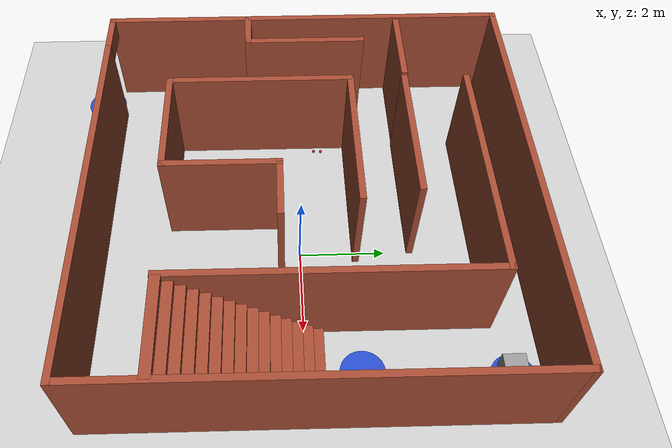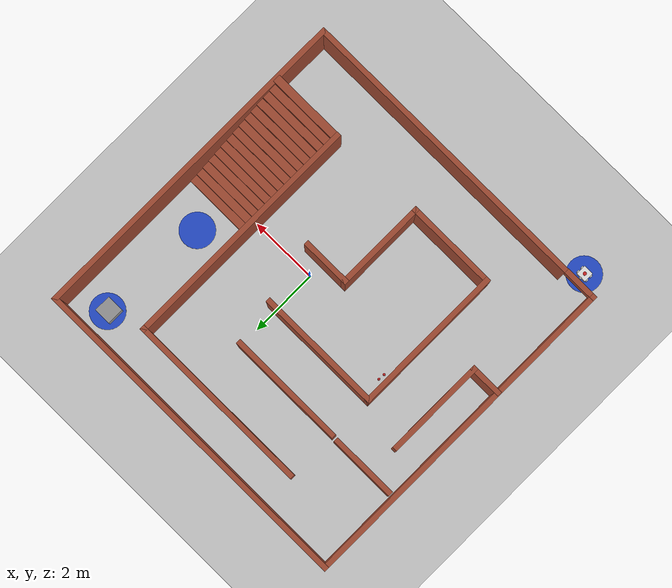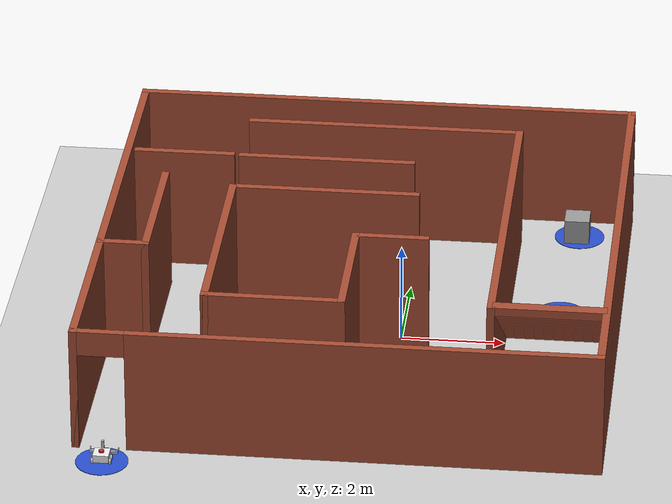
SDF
<sdf version="1.7">
 <world name="default">
  <light name="sun" type="directional">
   <pose>0 0 10 0 -0 0</pose>
   <diffuse>0.8 0.8 0.8 1</diffuse>
   <specular>0.2 0.2 0.2 1</specular>
   <attenuation>
    <range>1000</range>
    <constant>0.9</constant>
    <linear>0.01</linear>
    <quadratic>0.001</quadratic>
   </attenuation>
   <direction>-0.5 0.1 -0.9</direction>
   <spot><inner_angle>0</inner_angle><outer_angle>0</outer_angle><falloff>0</falloff></spot>
  </light>
  <model name="ground_plane">
   <static>1</static>
   <link name="link">
    <collision name="collision">
     <geometry><plane><normal>0 0 1</normal><size>100 100</size></plane></geometry>
     <surface>
      <contact><collide_bitmask>65535</collide_bitmask></contact>
      <friction><ode><mu>100</mu><mu2>50</mu2></ode></friction>
     </surface>
    </collision>
    <visual name="visual">
     <cast_shadows>0</cast_shadows>
     <geometry><plane><normal>0 0 1</normal><size>100 100</size></plane></geometry>
     <material>
      <script><uri>file://media/materials/scripts/gazebo.material</uri><name>Gazebo/Grey</name></script>
     </material>
    </visual>
   </link>
  </model>
  <gravity>0 0 -9.8</gravity>
  <magnetic_field>6e-06 2.3e-05 -4.2e-05</magnetic_field>
  <atmosphere type="adiabatic"/>
  <physics type="ode">
   <max_step_size>0.001</max_step_size>
   <real_time_factor>1</real_time_factor>
   <real_time_update_rate>1000</real_time_update_rate>
  </physics>
  <scene><ambient>0.4 0.4 0.4 1</ambient><background>0.7 0.7 0.7 1</background><shadows>1</shadows></scene>
  <audio><device>default</device></audio>
  <spherical_coordinates>
   <surface_model>EARTH_WGS84</surface_model>
   <latitude_deg>0</latitude_deg>
   <longitude_deg>0</longitude_deg>
   <elevation>0</elevation>
   <heading_deg>0</heading_deg>
  </spherical_coordinates>
  <model name="cricket_ball">
   <link name="link">
    <pose>0 0 0.0375 0 -0 0</pose>
    <inertial>
     <mass>0.1467</mass>
     <inertia>
      <ixx>8.25187e-05</ixx>
      <ixy>0</ixy>
      <ixz>0</ixz>
      <iyy>8.25187e-05</iyy>
      <iyz>0</iyz>
      <izz>8.25187e-05</izz>
     </inertia>
    </inertial>
    <collision name="collision">
     <geometry><sphere><radius>0.0375</radius></sphere></geometry>
     <surface>
      <contact>
       <poissons_ratio>0.347</poissons_ratio>
       <elastic_modulus>8.8e+09</elastic_modulus>
       <ode><kp>100000</kp><kd>100</kd><max_vel>100</max_vel><min_depth>0.001</min_depth></ode>
      </contact>
      <friction>
       <torsional>
        <coefficient>1</coefficient>
        <use_patch_radius>0</use_patch_radius>
        <surface_radius>0.01</surface_radius>
       </torsional>
      </friction>
     </surface>
    </collision>
    <visual name="visual">
     <geometry><sphere><radius>0.0375</radius></sphere></geometry>
     <material>
      <script><uri>file://media/materials/scripts/gazebo.material</uri><name>Gazebo/Red</name></script>
     </material>
    </visual>
    <velocity_decay><linear>0</linear><angular>0.005</angular></velocity_decay>
   </link>
   <pose>-3.24488 0.467417 -0.001014 0 -0 0</pose>
  </model>
  <model name="cricket_ball_0">
   <link name="link">
    <pose>0 0 0.0375 0 -0 0</pose>
    <inertial>
     <mass>0.1467</mass>
     <inertia>
      <ixx>8.25187e-05</ixx>
      <ixy>0</ixy>
      <ixz>0</ixz>
      <iyy>8.25187e-05</iyy>
      <iyz>0</iyz>
      <izz>8.25187e-05</izz>
     </inertia>
    </inertial>
    <collision name="collision">
     <geometry><sphere><radius>0.0375</radius></sphere></geometry>
     <surface>
      <contact>
       <poissons_ratio>0.347</poissons_ratio>
       <elastic_modulus>8.8e+09</elastic_modulus>
       <ode><kp>100000</kp><kd>100</kd><max_vel>100</max_vel><min_depth>0.001</min_depth></ode>
      </contact>
      <friction>
       <torsional>
        <coefficient>1</coefficient>
        <use_patch_radius>0</use_patch_radius>
        <surface_radius>0.01</surface_radius>
       </torsional>
      </friction>
     </surface>
    </collision>
    <visual name="visual">
     <geometry><sphere><radius>0.0375</radius></sphere></geometry>
     <material>
      <script><uri>file://media/materials/scripts/gazebo.material</uri><name>Gazebo/Red</name></script>
     </material>
    </visual>
    <velocity_decay><linear>0</linear><angular>0.005</angular></velocity_decay>
   </link>
   <pose>-3.22979 0.649662 -0.001014 0 -0 0</pose>
  </model>
  <model name="Green_Circle">
   <link name="link_0">
    <inertial>
     <mass>1</mass>
     <inertia><ixx>0.145833</ixx><ixy>0</ixy><ixz>0</ixz><iyy>0.145833</iyy><iyz>0</iyz><izz>0.125</izz></inertia>
    </inertial>
    <visual name="visual">
     <geometry><cylinder><radius>0.5</radius><length>0.01</length></cylinder></geometry>
     <material>
      <lighting>1</lighting>
      <script><uri>file://media/materials/scripts/gazebo.material</uri><name>Gazebo/Blue</name></script>
      <shader type="pixel"><normal_map>__default__</normal_map></shader>
      <ambient>0.18 0.761 0.494 1</ambient>
      <diffuse>0.18 0.761 0.494 1</diffuse>
      <specular>0.18 0.761 0.494 1</specular>
      <emissive>0 0 0 1</emissive>
     </material>
    </visual>
    <collision name="collision">
     <geometry><cylinder><radius>0.5</radius><length>0.01</length></cylinder></geometry>
     <surface>
      <friction>
       <ode><mu>1</mu><mu2>1</mu2><fdir1>0 0 0</fdir1><slip1>0</slip1><slip2>0</slip2></ode>
       <torsional>
        <coefficient>1</coefficient>
        <patch_radius>0</patch_radius>
        <surface_radius>0</surface_radius>
        <use_patch_radius>1</use_patch_radius>
        <ode><slip>0</slip></ode>
       </torsional>
      </friction>
      <bounce><restitution_coefficient>0</restitution_coefficient><threshold>1e+06</threshold></bounce>
      <contact>
       <collide_without_contact>0</collide_without_contact>
       <collide_without_contact_bitmask>1</collide_without_contact_bitmask>
       <collide_bitmask>1</collide_bitmask>
       <ode>
        <soft_cfm>0</soft_cfm>
        <soft_erp>0.2</soft_erp>
        <kp>1e+13</kp>
        <kd>1</kd>
        <max_vel>0.01</max_vel>
        <min_depth>0</min_depth>
       </ode>
       <bullet>
        <split_impulse>1</split_impulse>
        <split_impulse_penetration_threshold>-0.01</split_impulse_penetration_threshold>
        <soft_cfm>0</soft_cfm>
        <soft_erp>0.2</soft_erp>
        <kp>1e+13</kp>
        <kd>1</kd>
       </bullet>
      </contact>
     </surface>
    </collision>
   </link>
   <static>1</static>
   <pose>3.18631 4.46804 0 0 -0 0</pose>
  </model>
  <model name="Red_Circle">
   <link name="link_0">
    <inertial>
     <mass>1</mass>
     <inertia><ixx>0.145833</ixx><ixy>0</ixy><ixz>0</ixz><iyy>0.145833</iyy><iyz>0</iyz><izz>0.125</izz></inertia>
    </inertial>
    <visual name="visual">
     <geometry><cylinder><radius>0.5</radius><length>0.01</length></cylinder></geometry>
     <material>
      <lighting>1</lighting>
      <script><uri>file://media/materials/scripts/gazebo.material</uri><name>Gazebo/Blue</name></script>
      <shader type="pixel"><normal_map>__default__</normal_map></shader>
      <ambient>0.753 0.11 0.157 1</ambient>
      <diffuse>0.753 0.11 0.157 1</diffuse>
      <specular>0.753 0.11 0.157 1</specular>
      <emissive>0 0 0 1</emissive>
     </material>
    </visual>
    <collision name="collision">
     <geometry><cylinder><radius>0.5</radius><length>0.01</length></cylinder></geometry>
     <surface>
      <friction>
       <ode><mu>1</mu><mu2>1</mu2><fdir1>0 0 0</fdir1><slip1>0</slip1><slip2>0</slip2></ode>
       <torsional>
        <coefficient>1</coefficient>
        <patch_radius>0</patch_radius>
        <surface_radius>0</surface_radius>
        <use_patch_radius>1</use_patch_radius>
        <ode><slip>0</slip></ode>
       </torsional>
      </friction>
      <bounce><restitution_coefficient>0</restitution_coefficient><threshold>1e+06</threshold></bounce>
      <contact>
       <collide_without_contact>0</collide_without_contact>
       <collide_without_contact_bitmask>1</collide_without_contact_bitmask>
       <collide_bitmask>1</collide_bitmask>
       <ode>
        <soft_cfm>0</soft_cfm>
        <soft_erp>0.2</soft_erp>
        <kp>1e+13</kp>
        <kd>1</kd>
        <max_vel>0.01</max_vel>
        <min_depth>0</min_depth>
       </ode>
       <bullet>
        <split_impulse>1</split_impulse>
        <split_impulse_penetration_threshold>-0.01</split_impulse_penetration_threshold>
        <soft_cfm>0</soft_cfm>
        <soft_erp>0.2</soft_erp>
        <kp>1e+13</kp>
        <kd>1</kd>
       </bullet>
      </contact>
     </surface>
    </collision>
   </link>
   <static>1</static>
   <pose>3.01972 1.24629 0 0 -0 0</pose>
  </model>
  <model name="Blue_Circle_1">
   <link name="link_0">
    <inertial>
     <mass>1</mass>
     <inertia><ixx>0.145833</ixx><ixy>0</ixy><ixz>0</ixz><iyy>0.145833</iyy><iyz>0</iyz><izz>0.125</izz></inertia>
    </inertial>
    <visual name="visual">
     <geometry><cylinder><radius>0.5</radius><length>0.01</length></cylinder></geometry>
     <material>
      <lighting>1</lighting>
      <script><uri>file://media/materials/scripts/gazebo.material</uri><name>Gazebo/Blue</name></script>
      <shader type="pixel"><normal_map>__default__</normal_map></shader>
      <ambient>0.11 0.443 0.847 1</ambient>
      <diffuse>0.11 0.443 0.847 1</diffuse>
      <specular>0.11 0.443 0.847 1</specular>
      <emissive>0 0 0 1</emissive>
     </material>
    </visual>
    <collision name="collision">
     <geometry><cylinder><radius>0.5</radius><length>0.01</length></cylinder></geometry>
     <surface>
      <friction>
       <ode><mu>1</mu><mu2>1</mu2><fdir1>0 0 0</fdir1><slip1>0</slip1><slip2>0</slip2></ode>
       <torsional>
        <coefficient>1</coefficient>
        <patch_radius>0</patch_radius>
        <surface_radius>0</surface_radius>
        <use_patch_radius>1</use_patch_radius>
        <ode><slip>0</slip></ode>
       </torsional>
      </friction>
      <bounce><restitution_coefficient>0</restitution_coefficient><threshold>1e+06</threshold></bounce>
      <contact>
       <collide_without_contact>0</collide_without_contact>
       <collide_without_contact_bitmask>1</collide_without_contact_bitmask>
       <collide_bitmask>1</collide_bitmask>
       <ode>
        <soft_cfm>0</soft_cfm>
        <soft_erp>0.2</soft_erp>
        <kp>1e+13</kp>
        <kd>1</kd>
        <max_vel>0.01</max_vel>
        <min_depth>0</min_depth>
       </ode>
       <bullet>
        <split_impulse>1</split_impulse>
        <split_impulse_penetration_threshold>-0.01</split_impulse_penetration_threshold>
        <soft_cfm>0</soft_cfm>
        <soft_erp>0.2</soft_erp>
        <kp>1e+13</kp>
        <kd>1</kd>
       </bullet>
      </contact>
     </surface>
    </collision>
   </link>
   <static>1</static>
   <pose>-5.14268 -5.21167 0 0 -0 0</pose>
  </model>
  <model name="MazeFinal">
   <link name="Stairs_0">
    <visual name="Stairs_0_Visual_0">
     <pose>3.84922 0.083239 0.083333 0 -0 0</pose>
     <geometry><box><size>2.16243 0.233333 0.166667</size></box></geometry>
     <material>
      <script><uri>file://media/materials/scripts/gazebo.material</uri><name>Gazebo/Bricks</name></script>
      <ambient>1 1 1 1</ambient>
      <shader type="pixel"/>
     </material>
     <meta><layer>0</layer></meta>
    </visual>
    <visual name="Stairs_0_Visual_1">
     <pose>3.84922 -0.150095 0.25 0 -0 0</pose>
     <geometry><box><size>2.16243 0.233333 0.166667</size></box></geometry>
     <material>
      <script><uri>file://media/materials/scripts/gazebo.material</uri><name>Gazebo/Bricks</name></script>
      <ambient>1 1 1 1</ambient>
      <shader type="pixel"/>
     </material>
     <meta><layer>0</layer></meta>
    </visual>
    <visual name="Stairs_0_Visual_2">
     <pose>3.84922 -0.383428 0.416667 0 -0 0</pose>
     <geometry><box><size>2.16243 0.233333 0.166667</size></box></geometry>
     <material>
      <script><uri>file://media/materials/scripts/gazebo.material</uri><name>Gazebo/Bricks</name></script>
      <ambient>1 1 1 1</ambient>
      <shader type="pixel"/>
     </material>
     <meta><layer>0</layer></meta>
    </visual>
    <visual name="Stairs_0_Visual_3">
     <pose>3.84922 -0.616761 0.583333 0 -0 0</pose>
     <geometry><box><size>2.16243 0.233333 0.166667</size></box></geometry>
     <material>
      <script><uri>file://media/materials/scripts/gazebo.material</uri><name>Gazebo/Bricks</name></script>
      <ambient>1 1 1 1</ambient>
      <shader type="pixel"/>
     </material>
     <meta><layer>0</layer></meta>
    </visual>
    <visual name="Stairs_0_Visual_4">
     <pose>3.84922 -0.850095 0.75 0 -0 0</pose>
     <geometry><box><size>2.16243 0.233333 0.166667</size></box></geometry>
     <material>
      <script><uri>file://media/materials/scripts/gazebo.material</uri><name>Gazebo/Bricks</name></script>
      <ambient>1 1 1 1</ambient>
      <shader type="pixel"/>
     </material>
     <meta><layer>0</layer></meta>
    </visual>
    <visual name="Stairs_0_Visual_5">
     <pose>3.84922 -1.08343 0.916667 0 -0 0</pose>
     <geometry><box><size>2.16243 0.233333 0.166667</size></box></geometry>
     <material>
      <script><uri>file://media/materials/scripts/gazebo.material</uri><name>Gazebo/Bricks</name></script>
      <ambient>1 1 1 1</ambient>
      <shader type="pixel"/>
     </material>
     <meta><layer>0</layer></meta>
    </visual>
    <visual name="Stairs_0_Visual_6">
     <pose>3.84922 -1.31676 1.08333 0 -0 0</pose>
     <geometry><box><size>2.16243 0.233333 0.166667</size></box></geometry>
     <material>
      <script><uri>file://media/materials/scripts/gazebo.material</uri><name>Gazebo/Bricks</name></script>
      <ambient>1 1 1 1</ambient>
      <shader type="pixel"/>
     </material>
     <meta><layer>0</layer></meta>
    </visual>
    <visual name="Stairs_0_Visual_7">
     <pose>3.84922 -1.5501 1.25 0 -0 0</pose>
     <geometry><box><size>2.16243 0.233333 0.166667</size></box></geometry>
     <material>
      <script><uri>file://media/materials/scripts/gazebo.material</uri><name>Gazebo/Bricks</name></script>
      <ambient>1 1 1 1</ambient>
      <shader type="pixel"/>
     </material>
     <meta><layer>0</layer></meta>
    </visual>
    <visual name="Stairs_0_Visual_8">
     <pose>3.84922 -1.78343 1.41667 0 -0 0</pose>
     <geometry><box><size>2.16243 0.233333 0.166667</size></box></geometry>
     <material>
      <script><uri>file://media/materials/scripts/gazebo.material</uri><name>Gazebo/Bricks</name></script>
      <ambient>1 1 1 1</ambient>
      <shader type="pixel"/>
     </material>
     <meta><layer>0</layer></meta>
    </visual>
    <visual name="Stairs_0_Visual_9">
     <pose>3.84922 -2.01676 1.58333 0 -0 0</pose>
     <geometry><box><size>2.16243 0.233333 0.166667</size></box></geometry>
     <material>
      <script><uri>file://media/materials/scripts/gazebo.material</uri><name>Gazebo/Bricks</name></script>
      <ambient>1 1 1 1</ambient>
      <shader type="pixel"/>
     </material>
     <meta><layer>0</layer></meta>
    </visual>
    <visual name="Stairs_0_Visual_10">
     <pose>3.84922 -2.25009 1.75 0 -0 0</pose>
     <geometry><box><size>2.16243 0.233333 0.166667</size></box></geometry>
     <material>
      <script><uri>file://media/materials/scripts/gazebo.material</uri><name>Gazebo/Bricks</name></script>
      <ambient>1 1 1 1</ambient>
      <shader type="pixel"/>
     </material>
     <meta><layer>0</layer></meta>
    </visual>
    <visual name="Stairs_0_Visual_11">
     <pose>3.84922 -2.48343 1.91667 0 -0 0</pose>
     <geometry><box><size>2.16243 0.233333 0.166667</size></box></geometry>
     <material>
      <script><uri>file://media/materials/scripts/gazebo.material</uri><name>Gazebo/Bricks</name></script>
      <ambient>1 1 1 1</ambient>
      <shader type="pixel"/>
     </material>
     <meta><layer>0</layer></meta>
    </visual>
    <visual name="Stairs_0_Visual_12">
     <pose>3.84922 -2.71676 2.08333 0 -0 0</pose>
     <geometry><box><size>2.16243 0.233333 0.166667</size></box></geometry>
     <material>
      <script><uri>file://media/materials/scripts/gazebo.material</uri><name>Gazebo/Bricks</name></script>
      <ambient>1 1 1 1</ambient>
      <shader type="pixel"/>
     </material>
     <meta><layer>0</layer></meta>
    </visual>
    <visual name="Stairs_0_Visual_13">
     <pose>3.84922 -2.9501 2.25 0 -0 0</pose>
     <geometry><box><size>2.16243 0.233333 0.166667</size></box></geometry>
     <material>
      <script><uri>file://media/materials/scripts/gazebo.material</uri><name>Gazebo/Bricks</name></script>
      <ambient>1 1 1 1</ambient>
      <shader type="pixel"/>
     </material>
     <meta><layer>0</layer></meta>
    </visual>
    <visual name="Stairs_0_Visual_14">
     <pose>3.84922 -3.18343 2.41667 0 -0 0</pose>
     <geometry><box><size>2.16243 0.233333 0.166667</size></box></geometry>
     <material>
      <script><uri>file://media/materials/scripts/gazebo.material</uri><name>Gazebo/Bricks</name></script>
      <ambient>1 1 1 1</ambient>
      <shader type="pixel"/>
     </material>
     <meta><layer>0</layer></meta>
    </visual>
    <collision name="Stairs_0_Collision_0">
     <pose>3.84922 0.083239 0.083333 0 -0 0</pose>
     <geometry><box><size>2.16243 0.233333 0.166667</size></box></geometry>
     <surface>
      <friction>
       <ode><mu>1</mu><mu2>1</mu2><fdir1>0 0 0</fdir1><slip1>0</slip1><slip2>0</slip2></ode>
       <torsional>
        <coefficient>1</coefficient>
        <patch_radius>0</patch_radius>
        <surface_radius>0</surface_radius>
        <use_patch_radius>1</use_patch_radius>
        <ode><slip>0</slip></ode>
       </torsional>
      </friction>
      <bounce><restitution_coefficient>0</restitution_coefficient><threshold>1e+06</threshold></bounce>
      <contact>
       <collide_without_contact>0</collide_without_contact>
       <collide_without_contact_bitmask>1</collide_without_contact_bitmask>
       <collide_bitmask>1</collide_bitmask>
       <ode>
        <soft_cfm>0</soft_cfm>
        <soft_erp>0.2</soft_erp>
        <kp>1e+13</kp>
        <kd>1</kd>
        <max_vel>0.01</max_vel>
        <min_depth>0</min_depth>
       </ode>
       <bullet>
        <split_impulse>1</split_impulse>
        <split_impulse_penetration_threshold>-0.01</split_impulse_penetration_threshold>
        <soft_cfm>0</soft_cfm>
        <soft_erp>0.2</soft_erp>
        <kp>1e+13</kp>
        <kd>1</kd>
       </bullet>
      </contact>
     </surface>
    </collision>
    <collision name="Stairs_0_Collision_1">
     <pose>3.84922 -0.150095 0.25 0 -0 0</pose>
     <geometry><box><size>2.16243 0.233333 0.166667</size></box></geometry>
     <surface>
      <friction>
       <ode><mu>1</mu><mu2>1</mu2><fdir1>0 0 0</fdir1><slip1>0</slip1><slip2>0</slip2></ode>
       <torsional>
        <coefficient>1</coefficient>
        <patch_radius>0</patch_radius>
        <surface_radius>0</surface_radius>
        <use_patch_radius>1</use_patch_radius>
        <ode><slip>0</slip></ode>
       </torsional>
      </friction>
      <bounce><restitution_coefficient>0</restitution_coefficient><threshold>1e+06</threshold></bounce>
      <contact>
       <collide_without_contact>0</collide_without_contact>
       <collide_without_contact_bitmask>1</collide_without_contact_bitmask>
       <collide_bitmask>1</collide_bitmask>
       <ode>
        <soft_cfm>0</soft_cfm>
        <soft_erp>0.2</soft_erp>
        <kp>1e+13</kp>
        <kd>1</kd>
        <max_vel>0.01</max_vel>
        <min_depth>0</min_depth>
       </ode>
       <bullet>
        <split_impulse>1</split_impulse>
        <split_impulse_penetration_threshold>-0.01</split_impulse_penetration_threshold>
        <soft_cfm>0</soft_cfm>
        <soft_erp>0.2</soft_erp>
        <kp>1e+13</kp>
        <kd>1</kd>
       </bullet>
      </contact>
     </surface>
    </collision>
    <collision name="Stairs_0_Collision_2">
     <pose>3.84922 -0.383428 0.416667 0 -0 0</pose>
     <geometry><box><size>2.16243 0.233333 0.166667</size></box></geometry>
     <surface>
      <friction>
       <ode><mu>1</mu><mu2>1</mu2><fdir1>0 0 0</fdir1><slip1>0</slip1><slip2>0</slip2></ode>
       <torsional>
        <coefficient>1</coefficient>
        <patch_radius>0</patch_radius>
        <surface_radius>0</surface_radius>
        <use_patch_radius>1</use_patch_radius>
        <ode><slip>0</slip></ode>
       </torsional>
      </friction>
      <bounce><restitution_coefficient>0</restitution_coefficient><threshold>1e+06</threshold></bounce>
      <contact>
       <collide_without_contact>0</collide_without_contact>
       <collide_without_contact_bitmask>1</collide_without_contact_bitmask>
       <collide_bitmask>1</collide_bitmask>
       <ode>
        <soft_cfm>0</soft_cfm>
        <soft_erp>0.2</soft_erp>
        <kp>1e+13</kp>
        <kd>1</kd>
        <max_vel>0.01</max_vel>
        <min_depth>0</min_depth>
       </ode>
       <bullet>
        <split_impulse>1</split_impulse>
        <split_impulse_penetration_threshold>-0.01</split_impulse_penetration_threshold>
        <soft_cfm>0</soft_cfm>
        <soft_erp>0.2</soft_erp>
        <kp>1e+13</kp>
        <kd>1</kd>
       </bullet>
      </contact>
     </surface>
    </collision>
    <collision name="Stairs_0_Collision_3">
     <pose>3.84922 -0.616761 0.583333 0 -0 0</pose>
     <geometry><box><size>2.16243 0.233333 0.166667</size></box></geometry>
     <surface>
      <friction>
       <ode><mu>1</mu><mu2>1</mu2><fdir1>0 0 0</fdir1><slip1>0</slip1><slip2>0</slip2></ode>
       <torsional>
        <coefficient>1</coefficient>
        <patch_radius>0</patch_radius>
        <surface_radius>0</surface_radius>
        <use_patch_radius>1</use_patch_radius>
        <ode><slip>0</slip></ode>
       </torsional>
      </friction>
      <bounce><restitution_coefficient>0</restitution_coefficient><threshold>1e+06</threshold></bounce>
      <contact>
       <collide_without_contact>0</collide_without_contact>
       <collide_without_contact_bitmask>1</collide_without_contact_bitmask>
       <collide_bitmask>1</collide_bitmask>
       <ode>
        <soft_cfm>0</soft_cfm>
        <soft_erp>0.2</soft_erp>
        <kp>1e+13</kp>
        <kd>1</kd>
        <max_vel>0.01</max_vel>
        <min_depth>0</min_depth>
       </ode>
       <bullet>
        <split_impulse>1</split_impulse>
        <split_impulse_penetration_threshold>-0.01</split_impulse_penetration_threshold>
        <soft_cfm>0</soft_cfm>
        <soft_erp>0.2</soft_erp>
        <kp>1e+13</kp>
        <kd>1</kd>
       </bullet>
      </contact>
     </surface>
    </collision>
    <collision name="Stairs_0_Collision_4">
     <pose>3.84922 -0.850095 0.75 0 -0 0</pose>
     <geometry><box><size>2.16243 0.233333 0.166667</size></box></geometry>
     <surface>
      <friction>
       <ode><mu>1</mu><mu2>1</mu2><fdir1>0 0 0</fdir1><slip1>0</slip1><slip2>0</slip2></ode>
       <torsional>
        <coefficient>1</coefficient>
        <patch_radius>0</patch_radius>
        <surface_radius>0</surface_radius>
        <use_patch_radius>1</use_patch_radius>
        <ode><slip>0</slip></ode>
       </torsional>
      </friction>
      <bounce><restitution_coefficient>0</restitution_coefficient><threshold>1e+06</threshold></bounce>
      <contact>
       <collide_without_contact>0</collide_without_contact>
       <collide_without_contact_bitmask>1</collide_without_contact_bitmask>
       <collide_bitmask>1</collide_bitmask>
       <ode>
        <soft_cfm>0</soft_cfm>
        <soft_erp>0.2</soft_erp>
        <kp>1e+13</kp>
        <kd>1</kd>
        <max_vel>0.01</max_vel>
        <min_depth>0</min_depth>
       </ode>
       <bullet>
        <split_impulse>1</split_impulse>
        <split_impulse_penetration_threshold>-0.01</split_impulse_penetration_threshold>
        <soft_cfm>0</soft_cfm>
        <soft_erp>0.2</soft_erp>
        <kp>1e+13</kp>
        <kd>1</kd>
       </bullet>
      </contact>
     </surface>
    </collision>
    <collision name="Stairs_0_Collision_5">
     <pose>3.84922 -1.08343 0.916667 0 -0 0</pose>
     <geometry><box><size>2.16243 0.233333 0.166667</size></box></geometry>
     <surface>
      <friction>
       <ode><mu>1</mu><mu2>1</mu2><fdir1>0 0 0</fdir1><slip1>0</slip1><slip2>0</slip2></ode>
       <torsional>
        <coefficient>1</coefficient>
        <patch_radius>0</patch_radius>
        <surface_radius>0</surface_radius>
        <use_patch_radius>1</use_patch_radius>
        <ode><slip>0</slip></ode>
       </torsional>
      </friction>
      <bounce><restitution_coefficient>0</restitution_coefficient><threshold>1e+06</threshold></bounce>
      <contact>
       <collide_without_contact>0</collide_without_contact>
       <collide_without_contact_bitmask>1</collide_without_contact_bitmask>
       <collide_bitmask>1</collide_bitmask>
       <ode>
        <soft_cfm>0</soft_cfm>
        <soft_erp>0.2</soft_erp>
        <kp>1e+13</kp>
        <kd>1</kd>
        <max_vel>0.01</max_vel>
        <min_depth>0</min_depth>
       </ode>
       <bullet>
        <split_impulse>1</split_impulse>
        <split_impulse_penetration_threshold>-0.01</split_impulse_penetration_threshold>
        <soft_cfm>0</soft_cfm>
        <soft_erp>0.2</soft_erp>
        <kp>1e+13</kp>
        <kd>1</kd>
       </bullet>
      </contact>
     </surface>
    </collision>
    <collision name="Stairs_0_Collision_6">
     <pose>3.84922 -1.31676 1.08333 0 -0 0</pose>
     <geometry><box><size>2.16243 0.233333 0.166667</size></box></geometry>
     <surface>
      <friction>
       <ode><mu>1</mu><mu2>1</mu2><fdir1>0 0 0</fdir1><slip1>0</slip1><slip2>0</slip2></ode>
       <torsional>
        <coefficient>1</coefficient>
        <patch_radius>0</patch_radius>
        <surface_radius>0</surface_radius>
        <use_patch_radius>1</use_patch_radius>
        <ode><slip>0</slip></ode>
       </torsional>
      </friction>
      <bounce><restitution_coefficient>0</restitution_coefficient><threshold>1e+06</threshold></bounce>
      <contact>
       <collide_without_contact>0</collide_without_contact>
       <collide_without_contact_bitmask>1</collide_without_contact_bitmask>
       <collide_bitmask>1</collide_bitmask>
       <ode>
        <soft_cfm>0</soft_cfm>
        <soft_erp>0.2</soft_erp>
        <kp>1e+13</kp>
        <kd>1</kd>
        <max_vel>0.01</max_vel>
        <min_depth>0</min_depth>
       </ode>
       <bullet>
        <split_impulse>1</split_impulse>
        <split_impulse_penetration_threshold>-0.01</split_impulse_penetration_threshold>
        <soft_cfm>0</soft_cfm>
        <soft_erp>0.2</soft_erp>
        <kp>1e+13</kp>
        <kd>1</kd>
       </bullet>
      </contact>
     </surface>
    </collision>
    <collision name="Stairs_0_Collision_7">
     <pose>3.84922 -1.5501 1.25 0 -0 0</pose>
     <geometry><box><size>2.16243 0.233333 0.166667</size></box></geometry>
     <surface>
      <friction>
       <ode><mu>1</mu><mu2>1</mu2><fdir1>0 0 0</fdir1><slip1>0</slip1><slip2>0</slip2></ode>
       <torsional>
        <coefficient>1</coefficient>
        <patch_radius>0</patch_radius>
        <surface_radius>0</surface_radius>
        <use_patch_radius>1</use_patch_radius>
        <ode><slip>0</slip></ode>
       </torsional>
      </friction>
      <bounce><restitution_coefficient>0</restitution_coefficient><threshold>1e+06</threshold></bounce>
      <contact>
       <collide_without_contact>0</collide_without_contact>
       <collide_without_contact_bitmask>1</collide_without_contact_bitmask>
       <collide_bitmask>1</collide_bitmask>
       <ode>
        <soft_cfm>0</soft_cfm>
        <soft_erp>0.2</soft_erp>
        <kp>1e+13</kp>
        <kd>1</kd>
        <max_vel>0.01</max_vel>
        <min_depth>0</min_depth>
       </ode>
       <bullet>
        <split_impulse>1</split_impulse>
        <split_impulse_penetration_threshold>-0.01</split_impulse_penetration_threshold>
        <soft_cfm>0</soft_cfm>
        <soft_erp>0.2</soft_erp>
        <kp>1e+13</kp>
        <kd>1</kd>
       </bullet>
      </contact>
     </surface>
    </collision>
    <collision name="Stairs_0_Collision_8">
     <pose>3.84922 -1.78343 1.41667 0 -0 0</pose>
     <geometry><box><size>2.16243 0.233333 0.166667</size></box></geometry>
     <surface>
      <friction>
       <ode><mu>1</mu><mu2>1</mu2><fdir1>0 0 0</fdir1><slip1>0</slip1><slip2>0</slip2></ode>
       <torsional>
        <coefficient>1</coefficient>
        <patch_radius>0</patch_radius>
        <surface_radius>0</surface_radius>
        <use_patch_radius>1</use_patch_radius>
        <ode><slip>0</slip></ode>
       </torsional>
      </friction>
      <bounce><restitution_coefficient>0</restitution_coefficient><threshold>1e+06</threshold></bounce>
      <contact>
       <collide_without_contact>0</collide_without_contact>
       <collide_without_contact_bitmask>1</collide_without_contact_bitmask>
       <collide_bitmask>1</collide_bitmask>
       <ode>
        <soft_cfm>0</soft_cfm>
        <soft_erp>0.2</soft_erp>
        <kp>1e+13</kp>
        <kd>1</kd>
        <max_vel>0.01</max_vel>
        <min_depth>0</min_depth>
       </ode>
       <bullet>
        <split_impulse>1</split_impulse>
        <split_impulse_penetration_threshold>-0.01</split_impulse_penetration_threshold>
        <soft_cfm>0</soft_cfm>
        <soft_erp>0.2</soft_erp>
        <kp>1e+13</kp>
        <kd>1</kd>
       </bullet>
      </contact>
     </surface>
    </collision>
    <collision name="Stairs_0_Collision_9">
     <pose>3.84922 -2.01676 1.58333 0 -0 0</pose>
     <geometry><box><size>2.16243 0.233333 0.166667</size></box></geometry>
     <surface>
      <friction>
       <ode><mu>1</mu><mu2>1</mu2><fdir1>0 0 0</fdir1><slip1>0</slip1><slip2>0</slip2></ode>
       <torsional>
        <coefficient>1</coefficient>
        <patch_radius>0</patch_radius>
        <surface_radius>0</surface_radius>
        <use_patch_radius>1</use_patch_radius>
        <ode><slip>0</slip></ode>
       </torsional>
      </friction>
      <bounce><restitution_coefficient>0</restitution_coefficient><threshold>1e+06</threshold></bounce>
      <contact>
       <collide_without_contact>0</collide_without_contact>
       <collide_without_contact_bitmask>1</collide_without_contact_bitmask>
       <collide_bitmask>1</collide_bitmask>
       <ode>
        <soft_cfm>0</soft_cfm>
        <soft_erp>0.2</soft_erp>
        <kp>1e+13</kp>
        <kd>1</kd>
        <max_vel>0.01</max_vel>
        <min_depth>0</min_depth>
       </ode>
       <bullet>
        <split_impulse>1</split_impulse>
        <split_impulse_penetration_threshold>-0.01</split_impulse_penetration_threshold>
        <soft_cfm>0</soft_cfm>
        <soft_erp>0.2</soft_erp>
        <kp>1e+13</kp>
        <kd>1</kd>
       </bullet>
      </contact>
     </surface>
    </collision>
    <collision name="Stairs_0_Collision_10">
     <pose>3.84922 -2.25009 1.75 0 -0 0</pose>
     <geometry><box><size>2.16243 0.233333 0.166667</size></box></geometry>
     <surface>
      <friction>
       <ode><mu>1</mu><mu2>1</mu2><fdir1>0 0 0</fdir1><slip1>0</slip1><slip2>0</slip2></ode>
       <torsional>
        <coefficient>1</coefficient>
        <patch_radius>0</patch_radius>
        <surface_radius>0</surface_radius>
        <use_patch_radius>1</use_patch_radius>
        <ode><slip>0</slip></ode>
       </torsional>
      </friction>
      <bounce><restitution_coefficient>0</restitution_coefficient><threshold>1e+06</threshold></bounce>
      <contact>
       <collide_without_contact>0</collide_without_contact>
       <collide_without_contact_bitmask>1</collide_without_contact_bitmask>
       <collide_bitmask>1</collide_bitmask>
       <ode>
        <soft_cfm>0</soft_cfm>
        <soft_erp>0.2</soft_erp>
        <kp>1e+13</kp>
        <kd>1</kd>
        <max_vel>0.01</max_vel>
        <min_depth>0</min_depth>
       </ode>
       <bullet>
        <split_impulse>1</split_impulse>
        <split_impulse_penetration_threshold>-0.01</split_impulse_penetration_threshold>
        <soft_cfm>0</soft_cfm>
        <soft_erp>0.2</soft_erp>
        <kp>1e+13</kp>
        <kd>1</kd>
       </bullet>
      </contact>
     </surface>
    </collision>
    <collision name="Stairs_0_Collision_11">
     <pose>3.84922 -2.48343 1.91667 0 -0 0</pose>
     <geometry><box><size>2.16243 0.233333 0.166667</size></box></geometry>
     <surface>
      <friction>
       <ode><mu>1</mu><mu2>1</mu2><fdir1>0 0 0</fdir1><slip1>0</slip1><slip2>0</slip2></ode>
       <torsional>
        <coefficient>1</coefficient>
        <patch_radius>0</patch_radius>
        <surface_radius>0</surface_radius>
        <use_patch_radius>1</use_patch_radius>
        <ode><slip>0</slip></ode>
       </torsional>
      </friction>
      <bounce><restitution_coefficient>0</restitution_coefficient><threshold>1e+06</threshold></bounce>
      <contact>
       <collide_without_contact>0</collide_without_contact>
       <collide_without_contact_bitmask>1</collide_without_contact_bitmask>
       <collide_bitmask>1</collide_bitmask>
       <ode>
        <soft_cfm>0</soft_cfm>
        <soft_erp>0.2</soft_erp>
        <kp>1e+13</kp>
        <kd>1</kd>
        <max_vel>0.01</max_vel>
        <min_depth>0</min_depth>
       </ode>
       <bullet>
        <split_impulse>1</split_impulse>
        <split_impulse_penetration_threshold>-0.01</split_impulse_penetration_threshold>
        <soft_cfm>0</soft_cfm>
        <soft_erp>0.2</soft_erp>
        <kp>1e+13</kp>
        <kd>1</kd>
       </bullet>
      </contact>
     </surface>
    </collision>
    <collision name="Stairs_0_Collision_12">
     <pose>3.84922 -2.71676 2.08333 0 -0 0</pose>
     <geometry><box><size>2.16243 0.233333 0.166667</size></box></geometry>
     <surface>
      <friction>
       <ode><mu>1</mu><mu2>1</mu2><fdir1>0 0 0</fdir1><slip1>0</slip1><slip2>0</slip2></ode>
       <torsional>
        <coefficient>1</coefficient>
        <patch_radius>0</patch_radius>
        <surface_radius>0</surface_radius>
        <use_patch_radius>1</use_patch_radius>
        <ode><slip>0</slip></ode>
       </torsional>
      </friction>
      <bounce><restitution_coefficient>0</restitution_coefficient><threshold>1e+06</threshold></bounce>
      <contact>
       <collide_without_contact>0</collide_without_contact>
       <collide_without_contact_bitmask>1</collide_without_contact_bitmask>
       <collide_bitmask>1</collide_bitmask>
       <ode>
        <soft_cfm>0</soft_cfm>
        <soft_erp>0.2</soft_erp>
        <kp>1e+13</kp>
        <kd>1</kd>
        <max_vel>0.01</max_vel>
        <min_depth>0</min_depth>
       </ode>
       <bullet>
        <split_impulse>1</split_impulse>
        <split_impulse_penetration_threshold>-0.01</split_impulse_penetration_threshold>
        <soft_cfm>0</soft_cfm>
        <soft_erp>0.2</soft_erp>
        <kp>1e+13</kp>
        <kd>1</kd>
       </bullet>
      </contact>
     </surface>
    </collision>
    <collision name="Stairs_0_Collision_13">
     <pose>3.84922 -2.9501 2.25 0 -0 0</pose>
     <geometry><box><size>2.16243 0.233333 0.166667</size></box></geometry>
     <surface>
      <friction>
       <ode><mu>1</mu><mu2>1</mu2><fdir1>0 0 0</fdir1><slip1>0</slip1><slip2>0</slip2></ode>
       <torsional>
        <coefficient>1</coefficient>
        <patch_radius>0</patch_radius>
        <surface_radius>0</surface_radius>
        <use_patch_radius>1</use_patch_radius>
        <ode><slip>0</slip></ode>
       </torsional>
      </friction>
      <bounce><restitution_coefficient>0</restitution_coefficient><threshold>1e+06</threshold></bounce>
      <contact>
       <collide_without_contact>0</collide_without_contact>
       <collide_without_contact_bitmask>1</collide_without_contact_bitmask>
       <collide_bitmask>1</collide_bitmask>
       <ode>
        <soft_cfm>0</soft_cfm>
        <soft_erp>0.2</soft_erp>
        <kp>1e+13</kp>
        <kd>1</kd>
        <max_vel>0.01</max_vel>
        <min_depth>0</min_depth>
       </ode>
       <bullet>
        <split_impulse>1</split_impulse>
        <split_impulse_penetration_threshold>-0.01</split_impulse_penetration_threshold>
        <soft_cfm>0</soft_cfm>
        <soft_erp>0.2</soft_erp>
        <kp>1e+13</kp>
        <kd>1</kd>
       </bullet>
      </contact>
     </surface>
    </collision>
    <collision name="Stairs_0_Collision_14">
     <pose>3.84922 -3.18343 2.41667 0 -0 0</pose>
     <geometry><box><size>2.16243 0.233333 0.166667</size></box></geometry>
     <surface>
      <friction>
       <ode><mu>1</mu><mu2>1</mu2><fdir1>0 0 0</fdir1><slip1>0</slip1><slip2>0</slip2></ode>
       <torsional>
        <coefficient>1</coefficient>
        <patch_radius>0</patch_radius>
        <surface_radius>0</surface_radius>
        <use_patch_radius>1</use_patch_radius>
        <ode><slip>0</slip></ode>
       </torsional>
      </friction>
      <bounce><restitution_coefficient>0</restitution_coefficient><threshold>1e+06</threshold></bounce>
      <contact>
       <collide_without_contact>0</collide_without_contact>
       <collide_without_contact_bitmask>1</collide_without_contact_bitmask>
       <collide_bitmask>1</collide_bitmask>
       <ode>
        <soft_cfm>0</soft_cfm>
        <soft_erp>0.2</soft_erp>
        <kp>1e+13</kp>
        <kd>1</kd>
        <max_vel>0.01</max_vel>
        <min_depth>0</min_depth>
       </ode>
       <bullet>
        <split_impulse>1</split_impulse>
        <split_impulse_penetration_threshold>-0.01</split_impulse_penetration_threshold>
        <soft_cfm>0</soft_cfm>
        <soft_erp>0.2</soft_erp>
        <kp>1e+13</kp>
        <kd>1</kd>
       </bullet>
      </contact>
     </surface>
    </collision>
   </link>
   <link name="Wall_0">
    <pose>0 -4.925 0 0 -0 0</pose>
    <visual name="Wall_0_Visual_0">
     <pose>-4.93049 0 1.25 0 -0 0</pose>
     <geometry><box><size>0.139029 0.15 2.5</size></box></geometry>
     <material>
      <script><uri>file://media/materials/scripts/gazebo.material</uri><name>Gazebo/Bricks</name></script>
      <ambient>1 1 1 1</ambient>
      <shader type="pixel"/>
     </material>
     <meta><layer>0</layer></meta>
    </visual>
    <visual name="Wall_0_Visual_1">
     <pose>0.519515 0 1.25 0 -0 0</pose>
     <geometry><box><size>8.96097 0.15 2.5</size></box></geometry>
     <material>
      <script><uri>file://media/materials/scripts/gazebo.material</uri><name>Gazebo/Bricks</name></script>
      <ambient>1 1 1 1</ambient>
      <shader type="pixel"/>
     </material>
     <meta><layer>0</layer></meta>
    </visual>
    <visual name="Wall_0_Visual_2">
     <pose>-4.41097 0 2.25 0 -0 0</pose>
     <geometry><box><size>0.9 0.15 0.5</size></box></geometry>
     <material>
      <script><uri>file://media/materials/scripts/gazebo.material</uri><name>Gazebo/Bricks</name></script>
      <ambient>1 1 1 1</ambient>
      <shader type="pixel"/>
     </material>
     <meta><layer>0</layer></meta>
    </visual>
    <collision name="Wall_0_Collision_0">
     <pose>-4.93049 0 1.25 0 -0 0</pose>
     <geometry><box><size>0.139029 0.15 2.5</size></box></geometry>
     <surface>
      <friction>
       <ode><mu>1</mu><mu2>1</mu2><fdir1>0 0 0</fdir1><slip1>0</slip1><slip2>0</slip2></ode>
       <torsional>
        <coefficient>1</coefficient>
        <patch_radius>0</patch_radius>
        <surface_radius>0</surface_radius>
        <use_patch_radius>1</use_patch_radius>
        <ode><slip>0</slip></ode>
       </torsional>
      </friction>
      <bounce><restitution_coefficient>0</restitution_coefficient><threshold>1e+06</threshold></bounce>
      <contact>
       <collide_without_contact>0</collide_without_contact>
       <collide_without_contact_bitmask>1</collide_without_contact_bitmask>
       <collide_bitmask>1</collide_bitmask>
       <ode>
        <soft_cfm>0</soft_cfm>
        <soft_erp>0.2</soft_erp>
        <kp>1e+13</kp>
        <kd>1</kd>
        <max_vel>0.01</max_vel>
        <min_depth>0</min_depth>
       </ode>
       <bullet>
        <split_impulse>1</split_impulse>
        <split_impulse_penetration_threshold>-0.01</split_impulse_penetration_threshold>
        <soft_cfm>0</soft_cfm>
        <soft_erp>0.2</soft_erp>
        <kp>1e+13</kp>
        <kd>1</kd>
       </bullet>
      </contact>
     </surface>
    </collision>
    <collision name="Wall_0_Collision_1">
     <pose>0.519515 0 1.25 0 -0 0</pose>
     <geometry><box><size>8.96097 0.15 2.5</size></box></geometry>
     <surface>
      <friction>
       <ode><mu>1</mu><mu2>1</mu2><fdir1>0 0 0</fdir1><slip1>0</slip1><slip2>0</slip2></ode>
       <torsional>
        <coefficient>1</coefficient>
        <patch_radius>0</patch_radius>
        <surface_radius>0</surface_radius>
        <use_patch_radius>1</use_patch_radius>
        <ode><slip>0</slip></ode>
       </torsional>
      </friction>
      <bounce><restitution_coefficient>0</restitution_coefficient><threshold>1e+06</threshold></bounce>
      <contact>
       <collide_without_contact>0</collide_without_contact>
       <collide_without_contact_bitmask>1</collide_without_contact_bitmask>
       <collide_bitmask>1</collide_bitmask>
       <ode>
        <soft_cfm>0</soft_cfm>
        <soft_erp>0.2</soft_erp>
        <kp>1e+13</kp>
        <kd>1</kd>
        <max_vel>0.01</max_vel>
        <min_depth>0</min_depth>
       </ode>
       <bullet>
        <split_impulse>1</split_impulse>
        <split_impulse_penetration_threshold>-0.01</split_impulse_penetration_threshold>
        <soft_cfm>0</soft_cfm>
        <soft_erp>0.2</soft_erp>
        <kp>1e+13</kp>
        <kd>1</kd>
       </bullet>
      </contact>
     </surface>
    </collision>
    <collision name="Wall_0_Collision_2">
     <pose>-4.41097 0 2.25 0 -0 0</pose>
     <geometry><box><size>0.9 0.15 0.5</size></box></geometry>
     <surface>
      <friction>
       <ode><mu>1</mu><mu2>1</mu2><fdir1>0 0 0</fdir1><slip1>0</slip1><slip2>0</slip2></ode>
       <torsional>
        <coefficient>1</coefficient>
        <patch_radius>0</patch_radius>
        <surface_radius>0</surface_radius>
        <use_patch_radius>1</use_patch_radius>
        <ode><slip>0</slip></ode>
       </torsional>
      </friction>
      <bounce><restitution_coefficient>0</restitution_coefficient><threshold>1e+06</threshold></bounce>
      <contact>
       <collide_without_contact>0</collide_without_contact>
       <collide_without_contact_bitmask>1</collide_without_contact_bitmask>
       <collide_bitmask>1</collide_bitmask>
       <ode>
        <soft_cfm>0</soft_cfm>
        <soft_erp>0.2</soft_erp>
        <kp>1e+13</kp>
        <kd>1</kd>
        <max_vel>0.01</max_vel>
        <min_depth>0</min_depth>
       </ode>
       <bullet>
        <split_impulse>1</split_impulse>
        <split_impulse_penetration_threshold>-0.01</split_impulse_penetration_threshold>
        <soft_cfm>0</soft_cfm>
        <soft_erp>0.2</soft_erp>
        <kp>1e+13</kp>
        <kd>1</kd>
       </bullet>
      </contact>
     </surface>
    </collision>
   </link>
   <link name="Wall_1">
    <pose>4.925 0 0 0 -0 1.5708</pose>
    <visual name="Wall_1_Visual">
     <pose>0 0 1.25 0 -0 0</pose>
     <geometry><box><size>10 0.15 2.5</size></box></geometry>
     <material>
      <script><uri>file://media/materials/scripts/gazebo.material</uri><name>Gazebo/Bricks</name></script>
      <ambient>1 1 1 1</ambient>
      <shader type="pixel"/>
     </material>
     <meta><layer>0</layer></meta>
    </visual>
    <collision name="Wall_1_Collision">
     <pose>0 0 1.25 0 -0 0</pose>
     <geometry><box><size>10 0.15 2.5</size></box></geometry>
     <surface>
      <friction>
       <ode><mu>1</mu><mu2>1</mu2><fdir1>0 0 0</fdir1><slip1>0</slip1><slip2>0</slip2></ode>
       <torsional>
        <coefficient>1</coefficient>
        <patch_radius>0</patch_radius>
        <surface_radius>0</surface_radius>
        <use_patch_radius>1</use_patch_radius>
        <ode><slip>0</slip></ode>
       </torsional>
      </friction>
      <bounce><restitution_coefficient>0</restitution_coefficient><threshold>1e+06</threshold></bounce>
      <contact>
       <collide_without_contact>0</collide_without_contact>
       <collide_without_contact_bitmask>1</collide_without_contact_bitmask>
       <collide_bitmask>1</collide_bitmask>
       <ode>
        <soft_cfm>0</soft_cfm>
        <soft_erp>0.2</soft_erp>
        <kp>1e+13</kp>
        <kd>1</kd>
        <max_vel>0.01</max_vel>
        <min_depth>0</min_depth>
       </ode>
       <bullet>
        <split_impulse>1</split_impulse>
        <split_impulse_penetration_threshold>-0.01</split_impulse_penetration_threshold>
        <soft_cfm>0</soft_cfm>
        <soft_erp>0.2</soft_erp>
        <kp>1e+13</kp>
        <kd>1</kd>
       </bullet>
      </contact>
     </surface>
    </collision>
   </link>
   <link name="Wall_10">
    <pose>-0.96091 2.36545 0 0 -0 0</pose>
    <visual name="Wall_10_Visual">
     <pose>0 0 1.25 0 -0 0</pose>
     <geometry><box><size>3.5 0.15 2.5</size></box></geometry>
     <material>
      <script><uri>file://media/materials/scripts/gazebo.material</uri><name>Gazebo/Bricks</name></script>
      <ambient>1 1 1 1</ambient>
      <shader type="pixel"/>
     </material>
     <meta><layer>0</layer></meta>
    </visual>
    <collision name="Wall_10_Collision">
     <pose>0 0 1.25 0 -0 0</pose>
     <geometry><box><size>3.5 0.15 2.5</size></box></geometry>
     <surface>
      <friction>
       <ode><mu>1</mu><mu2>1</mu2><fdir1>0 0 0</fdir1><slip1>0</slip1><slip2>0</slip2></ode>
       <torsional>
        <coefficient>1</coefficient>
        <patch_radius>0</patch_radius>
        <surface_radius>0</surface_radius>
        <use_patch_radius>1</use_patch_radius>
        <ode><slip>0</slip></ode>
       </torsional>
      </friction>
      <bounce><restitution_coefficient>0</restitution_coefficient><threshold>1e+06</threshold></bounce>
      <contact>
       <collide_without_contact>0</collide_without_contact>
       <collide_without_contact_bitmask>1</collide_without_contact_bitmask>
       <collide_bitmask>1</collide_bitmask>
       <ode>
        <soft_cfm>0</soft_cfm>
        <soft_erp>0.2</soft_erp>
        <kp>1e+13</kp>
        <kd>1</kd>
        <max_vel>0.01</max_vel>
        <min_depth>0</min_depth>
       </ode>
       <bullet>
        <split_impulse>1</split_impulse>
        <split_impulse_penetration_threshold>-0.01</split_impulse_penetration_threshold>
        <soft_cfm>0</soft_cfm>
        <soft_erp>0.2</soft_erp>
        <kp>1e+13</kp>
        <kd>1</kd>
       </bullet>
      </contact>
     </surface>
    </collision>
   </link>
   <link name="Wall_13">
    <pose>0.06968 3.86438 0 0 -0 0</pose>
    <visual name="Wall_13_Visual">
     <pose>0 0 1.25 0 -0 0</pose>
     <geometry><box><size>5.5 0.15 2.5</size></box></geometry>
     <material>
      <script><uri>file://media/materials/scripts/gazebo.material</uri><name>Gazebo/Bricks</name></script>
      <ambient>1 1 1 1</ambient>
      <shader type="pixel"/>
     </material>
     <meta><layer>0</layer></meta>
    </visual>
    <collision name="Wall_13_Collision">
     <pose>0 0 1.25 0 -0 0</pose>
     <geometry><box><size>5.5 0.15 2.5</size></box></geometry>
     <surface>
      <friction>
       <ode><mu>1</mu><mu2>1</mu2><fdir1>0 0 0</fdir1><slip1>0</slip1><slip2>0</slip2></ode>
       <torsional>
        <coefficient>1</coefficient>
        <patch_radius>0</patch_radius>
        <surface_radius>0</surface_radius>
        <use_patch_radius>1</use_patch_radius>
        <ode><slip>0</slip></ode>
       </torsional>
      </friction>
      <bounce><restitution_coefficient>0</restitution_coefficient><threshold>1e+06</threshold></bounce>
      <contact>
       <collide_without_contact>0</collide_without_contact>
       <collide_without_contact_bitmask>1</collide_without_contact_bitmask>
       <collide_bitmask>1</collide_bitmask>
       <ode>
        <soft_cfm>0</soft_cfm>
        <soft_erp>0.2</soft_erp>
        <kp>1e+13</kp>
        <kd>1</kd>
        <max_vel>0.01</max_vel>
        <min_depth>0</min_depth>
       </ode>
       <bullet>
        <split_impulse>1</split_impulse>
        <split_impulse_penetration_threshold>-0.01</split_impulse_penetration_threshold>
        <soft_cfm>0</soft_cfm>
        <soft_erp>0.2</soft_erp>
        <kp>1e+13</kp>
        <kd>1</kd>
       </bullet>
      </contact>
     </surface>
    </collision>
   </link>
   <link name="Wall_14">
    <pose>2.74468 0.314376 0 0 0 -1.5708</pose>
    <visual name="Wall_14_Visual">
     <pose>0 0 1.25 0 -0 0</pose>
     <geometry><box><size>7.25 0.15 2.5</size></box></geometry>
     <material>
      <script><uri>file://media/materials/scripts/gazebo.material</uri><name>Gazebo/Bricks</name></script>
      <ambient>1 1 1 1</ambient>
      <shader type="pixel"/>
     </material>
     <meta><layer>0</layer></meta>
    </visual>
    <collision name="Wall_14_Collision">
     <pose>0 0 1.25 0 -0 0</pose>
     <geometry><box><size>7.25 0.15 2.5</size></box></geometry>
     <surface>
      <friction>
       <ode><mu>1</mu><mu2>1</mu2><fdir1>0 0 0</fdir1><slip1>0</slip1><slip2>0</slip2></ode>
       <torsional>
        <coefficient>1</coefficient>
        <patch_radius>0</patch_radius>
        <surface_radius>0</surface_radius>
        <use_patch_radius>1</use_patch_radius>
        <ode><slip>0</slip></ode>
       </torsional>
      </friction>
      <bounce><restitution_coefficient>0</restitution_coefficient><threshold>1e+06</threshold></bounce>
      <contact>
       <collide_without_contact>0</collide_without_contact>
       <collide_without_contact_bitmask>1</collide_without_contact_bitmask>
       <collide_bitmask>1</collide_bitmask>
       <ode>
        <soft_cfm>0</soft_cfm>
        <soft_erp>0.2</soft_erp>
        <kp>1e+13</kp>
        <kd>1</kd>
        <max_vel>0.01</max_vel>
        <min_depth>0</min_depth>
       </ode>
       <bullet>
        <split_impulse>1</split_impulse>
        <split_impulse_penetration_threshold>-0.01</split_impulse_penetration_threshold>
        <soft_cfm>0</soft_cfm>
        <soft_erp>0.2</soft_erp>
        <kp>1e+13</kp>
        <kd>1</kd>
       </bullet>
      </contact>
     </surface>
    </collision>
   </link>
   <link name="Wall_16">
    <pose>-1.36922 -3.29308 0 0 -0 0</pose>
    <visual name="Wall_16_Visual">
     <pose>0 0 1.25 0 -0 0</pose>
     <geometry><box><size>2.75 0.15 2.5</size></box></geometry>
     <material>
      <script><uri>file://media/materials/scripts/gazebo.material</uri><name>Gazebo/Bricks</name></script>
      <ambient>1 1 1 1</ambient>
      <shader type="pixel"/>
     </material>
     <meta><layer>0</layer></meta>
    </visual>
    <collision name="Wall_16_Collision">
     <pose>0 0 1.25 0 -0 0</pose>
     <geometry><box><size>2.75 0.15 2.5</size></box></geometry>
     <surface>
      <friction>
       <ode><mu>1</mu><mu2>1</mu2><fdir1>0 0 0</fdir1><slip1>0</slip1><slip2>0</slip2></ode>
       <torsional>
        <coefficient>1</coefficient>
        <patch_radius>0</patch_radius>
        <surface_radius>0</surface_radius>
        <use_patch_radius>1</use_patch_radius>
        <ode><slip>0</slip></ode>
       </torsional>
      </friction>
      <bounce><restitution_coefficient>0</restitution_coefficient><threshold>1e+06</threshold></bounce>
      <contact>
       <collide_without_contact>0</collide_without_contact>
       <collide_without_contact_bitmask>1</collide_without_contact_bitmask>
       <collide_bitmask>1</collide_bitmask>
       <ode>
        <soft_cfm>0</soft_cfm>
        <soft_erp>0.2</soft_erp>
        <kp>1e+13</kp>
        <kd>1</kd>
        <max_vel>0.01</max_vel>
        <min_depth>0</min_depth>
       </ode>
       <bullet>
        <split_impulse>1</split_impulse>
        <split_impulse_penetration_threshold>-0.01</split_impulse_penetration_threshold>
        <soft_cfm>0</soft_cfm>
        <soft_erp>0.2</soft_erp>
        <kp>1e+13</kp>
        <kd>1</kd>
       </bullet>
      </contact>
     </surface>
    </collision>
   </link>
   <link name="Wall_17">
    <pose>-0.069221 -1.99307 0 0 -0 1.5708</pose>
    <visual name="Wall_17_Visual">
     <pose>0 0 1.25 0 -0 0</pose>
     <geometry><box><size>2.75 0.15 2.5</size></box></geometry>
     <material>
      <script><uri>file://media/materials/scripts/gazebo.material</uri><name>Gazebo/Bricks</name></script>
      <ambient>1 1 1 1</ambient>
      <shader type="pixel"/>
     </material>
     <meta><layer>0</layer></meta>
    </visual>
    <collision name="Wall_17_Collision">
     <pose>0 0 1.25 0 -0 0</pose>
     <geometry><box><size>2.75 0.15 2.5</size></box></geometry>
     <surface>
      <friction>
       <ode><mu>1</mu><mu2>1</mu2><fdir1>0 0 0</fdir1><slip1>0</slip1><slip2>0</slip2></ode>
       <torsional>
        <coefficient>1</coefficient>
        <patch_radius>0</patch_radius>
        <surface_radius>0</surface_radius>
        <use_patch_radius>1</use_patch_radius>
        <ode><slip>0</slip></ode>
       </torsional>
      </friction>
      <bounce><restitution_coefficient>0</restitution_coefficient><threshold>1e+06</threshold></bounce>
      <contact>
       <collide_without_contact>0</collide_without_contact>
       <collide_without_contact_bitmask>1</collide_without_contact_bitmask>
       <collide_bitmask>1</collide_bitmask>
       <ode>
        <soft_cfm>0</soft_cfm>
        <soft_erp>0.2</soft_erp>
        <kp>1e+13</kp>
        <kd>1</kd>
        <max_vel>0.01</max_vel>
        <min_depth>0</min_depth>
       </ode>
       <bullet>
        <split_impulse>1</split_impulse>
        <split_impulse_penetration_threshold>-0.01</split_impulse_penetration_threshold>
        <soft_cfm>0</soft_cfm>
        <soft_erp>0.2</soft_erp>
        <kp>1e+13</kp>
        <kd>1</kd>
       </bullet>
      </contact>
     </surface>
    </collision>
   </link>
   <link name="Wall_18">
    <pose>0.605779 -0.693076 0 0 -0 0</pose>
    <visual name="Wall_18_Visual">
     <pose>0 0 1.25 0 -0 0</pose>
     <geometry><box><size>1.5 0.15 2.5</size></box></geometry>
     <material>
      <script><uri>file://media/materials/scripts/gazebo.material</uri><name>Gazebo/Bricks</name></script>
      <ambient>1 1 1 1</ambient>
      <shader type="pixel"/>
     </material>
     <meta><layer>0</layer></meta>
    </visual>
    <collision name="Wall_18_Collision">
     <pose>0 0 1.25 0 -0 0</pose>
     <geometry><box><size>1.5 0.15 2.5</size></box></geometry>
     <surface>
      <friction>
       <ode><mu>1</mu><mu2>1</mu2><fdir1>0 0 0</fdir1><slip1>0</slip1><slip2>0</slip2></ode>
       <torsional>
        <coefficient>1</coefficient>
        <patch_radius>0</patch_radius>
        <surface_radius>0</surface_radius>
        <use_patch_radius>1</use_patch_radius>
        <ode><slip>0</slip></ode>
       </torsional>
      </friction>
      <bounce><restitution_coefficient>0</restitution_coefficient><threshold>1e+06</threshold></bounce>
      <contact>
       <collide_without_contact>0</collide_without_contact>
       <collide_without_contact_bitmask>1</collide_without_contact_bitmask>
       <collide_bitmask>1</collide_bitmask>
       <ode>
        <soft_cfm>0</soft_cfm>
        <soft_erp>0.2</soft_erp>
        <kp>1e+13</kp>
        <kd>1</kd>
        <max_vel>0.01</max_vel>
        <min_depth>0</min_depth>
       </ode>
       <bullet>
        <split_impulse>1</split_impulse>
        <split_impulse_penetration_threshold>-0.01</split_impulse_penetration_threshold>
        <soft_cfm>0</soft_cfm>
        <soft_erp>0.2</soft_erp>
        <kp>1e+13</kp>
        <kd>1</kd>
       </bullet>
      </contact>
     </surface>
    </collision>
   </link>
   <link name="Wall_2">
    <pose>0 4.925 0 0 -0 3.14159</pose>
    <inertial>
     <mass>1</mass>
     <inertia><ixx>1</ixx><ixy>0</ixy><ixz>0</ixz><iyy>1</iyy><iyz>0</iyz><izz>1</izz></inertia>
    </inertial>
    <visual name="Wall_2_Visual">
     <pose>0 0 1.25 0 -0 0</pose>
     <geometry><box><size>10 0.15 2.5</size></box></geometry>
     <material>
      <script><uri>file://media/materials/scripts/gazebo.material</uri><name>Gazebo/Bricks</name></script>
      <ambient>1 1 1 1</ambient>
      <shader type="pixel"><normal_map>__default__</normal_map></shader>
     </material>
     <meta><layer>0</layer></meta>
    </visual>
    <collision name="Wall_2_Collision">
     <pose>0 0 1.25 0 -0 0</pose>
     <geometry><box><size>10 0.15 2.5</size></box></geometry>
     <surface>
      <friction>
       <ode><mu>1</mu><mu2>1</mu2><fdir1>0 0 0</fdir1><slip1>0</slip1><slip2>0</slip2></ode>
       <torsional>
        <coefficient>1</coefficient>
        <patch_radius>0</patch_radius>
        <surface_radius>0</surface_radius>
        <use_patch_radius>1</use_patch_radius>
        <ode><slip>0</slip></ode>
       </torsional>
      </friction>
      <bounce><restitution_coefficient>0</restitution_coefficient><threshold>1e+06</threshold></bounce>
      <contact>
       <collide_without_contact>0</collide_without_contact>
       <collide_without_contact_bitmask>1</collide_without_contact_bitmask>
       <collide_bitmask>1</collide_bitmask>
       <ode>
        <soft_cfm>0</soft_cfm>
        <soft_erp>0.2</soft_erp>
        <kp>1e+13</kp>
        <kd>1</kd>
        <max_vel>0.01</max_vel>
        <min_depth>0</min_depth>
       </ode>
       <bullet>
        <split_impulse>1</split_impulse>
        <split_impulse_penetration_threshold>-0.01</split_impulse_penetration_threshold>
        <soft_cfm>0</soft_cfm>
        <soft_erp>0.2</soft_erp>
        <kp>1e+13</kp>
        <kd>1</kd>
       </bullet>
      </contact>
     </surface>
    </collision>
   </link>
   <link name="Wall_20">
    <pose>-4.47459 -1.42773 0 0 -0 0</pose>
    <visual name="Wall_20_Visual">
     <pose>0 0 1.25 0 -0 0</pose>
     <geometry><box><size>1 0.15 2.5</size></box></geometry>
     <material>
      <script><uri>file://media/materials/scripts/gazebo.material</uri><name>Gazebo/Bricks</name></script>
      <ambient>1 1 1 1</ambient>
      <shader type="pixel"/>
     </material>
     <meta><layer>0</layer></meta>
    </visual>
    <collision name="Wall_20_Collision">
     <pose>0 0 1.25 0 -0 0</pose>
     <geometry><box><size>1 0.15 2.5</size></box></geometry>
     <surface>
      <friction>
       <ode><mu>1</mu><mu2>1</mu2><fdir1>0 0 0</fdir1><slip1>0</slip1><slip2>0</slip2></ode>
       <torsional>
        <coefficient>1</coefficient>
        <patch_radius>0</patch_radius>
        <surface_radius>0</surface_radius>
        <use_patch_radius>1</use_patch_radius>
        <ode><slip>0</slip></ode>
       </torsional>
      </friction>
      <bounce><restitution_coefficient>0</restitution_coefficient><threshold>1e+06</threshold></bounce>
      <contact>
       <collide_without_contact>0</collide_without_contact>
       <collide_without_contact_bitmask>1</collide_without_contact_bitmask>
       <collide_bitmask>1</collide_bitmask>
       <ode>
        <soft_cfm>0</soft_cfm>
        <soft_erp>0.2</soft_erp>
        <kp>1e+13</kp>
        <kd>1</kd>
        <max_vel>0.01</max_vel>
        <min_depth>0</min_depth>
       </ode>
       <bullet>
        <split_impulse>1</split_impulse>
        <split_impulse_penetration_threshold>-0.01</split_impulse_penetration_threshold>
        <soft_cfm>0</soft_cfm>
        <soft_erp>0.2</soft_erp>
        <kp>1e+13</kp>
        <kd>1</kd>
       </bullet>
      </contact>
     </surface>
    </collision>
   </link>
   <link name="Wall_21">
    <pose>-4.04959 -0.002734 0 0 -0 1.5708</pose>
    <visual name="Wall_21_Visual">
     <pose>0 0 1.25 0 -0 0</pose>
     <geometry><box><size>3 0.15 2.5</size></box></geometry>
     <material>
      <script><uri>file://media/materials/scripts/gazebo.material</uri><name>Gazebo/Bricks</name></script>
      <ambient>1 1 1 1</ambient>
      <shader type="pixel"/>
     </material>
     <meta><layer>0</layer></meta>
    </visual>
    <collision name="Wall_21_Collision">
     <pose>0 0 1.25 0 -0 0</pose>
     <geometry><box><size>3 0.15 2.5</size></box></geometry>
     <surface>
      <friction>
       <ode><mu>1</mu><mu2>1</mu2><fdir1>0 0 0</fdir1><slip1>0</slip1><slip2>0</slip2></ode>
       <torsional>
        <coefficient>1</coefficient>
        <patch_radius>0</patch_radius>
        <surface_radius>0</surface_radius>
        <use_patch_radius>1</use_patch_radius>
        <ode><slip>0</slip></ode>
       </torsional>
      </friction>
      <bounce><restitution_coefficient>0</restitution_coefficient><threshold>1e+06</threshold></bounce>
      <contact>
       <collide_without_contact>0</collide_without_contact>
       <collide_without_contact_bitmask>1</collide_without_contact_bitmask>
       <collide_bitmask>1</collide_bitmask>
       <ode>
        <soft_cfm>0</soft_cfm>
        <soft_erp>0.2</soft_erp>
        <kp>1e+13</kp>
        <kd>1</kd>
        <max_vel>0.01</max_vel>
        <min_depth>0</min_depth>
       </ode>
       <bullet>
        <split_impulse>1</split_impulse>
        <split_impulse_penetration_threshold>-0.01</split_impulse_penetration_threshold>
        <soft_cfm>0</soft_cfm>
        <soft_erp>0.2</soft_erp>
        <kp>1e+13</kp>
        <kd>1</kd>
       </bullet>
      </contact>
     </surface>
    </collision>
   </link>
   <link name="Wall_3">
    <pose>-4.925 0 0 0 0 -1.5708</pose>
    <visual name="Wall_3_Visual">
     <pose>0 0 1.25 0 -0 0</pose>
     <geometry><box><size>10 0.15 2.5</size></box></geometry>
     <material>
      <script><uri>file://media/materials/scripts/gazebo.material</uri><name>Gazebo/Bricks</name></script>
      <ambient>1 1 1 1</ambient>
      <shader type="pixel"/>
     </material>
     <meta><layer>0</layer></meta>
    </visual>
    <collision name="Wall_3_Collision">
     <pose>0 0 1.25 0 -0 0</pose>
     <geometry><box><size>10 0.15 2.5</size></box></geometry>
     <surface>
      <friction>
       <ode><mu>1</mu><mu2>1</mu2><fdir1>0 0 0</fdir1><slip1>0</slip1><slip2>0</slip2></ode>
       <torsional>
        <coefficient>1</coefficient>
        <patch_radius>0</patch_radius>
        <surface_radius>0</surface_radius>
        <use_patch_radius>1</use_patch_radius>
        <ode><slip>0</slip></ode>
       </torsional>
      </friction>
      <bounce><restitution_coefficient>0</restitution_coefficient><threshold>1e+06</threshold></bounce>
      <contact>
       <collide_without_contact>0</collide_without_contact>
       <collide_without_contact_bitmask>1</collide_without_contact_bitmask>
       <collide_bitmask>1</collide_bitmask>
       <ode>
        <soft_cfm>0</soft_cfm>
        <soft_erp>0.2</soft_erp>
        <kp>1e+13</kp>
        <kd>1</kd>
        <max_vel>0.01</max_vel>
        <min_depth>0</min_depth>
       </ode>
       <bullet>
        <split_impulse>1</split_impulse>
        <split_impulse_penetration_threshold>-0.01</split_impulse_penetration_threshold>
        <soft_cfm>0</soft_cfm>
        <soft_erp>0.2</soft_erp>
        <kp>1e+13</kp>
        <kd>1</kd>
       </bullet>
      </contact>
     </surface>
    </collision>
   </link>
   <link name="Wall_7">
    <pose>-2.66922 -1.11808 0 0 -0 1.5708</pose>
    <visual name="Wall_7_Visual">
     <pose>0 0 1.25 0 -0 0</pose>
     <geometry><box><size>4.5 0.15 2.5</size></box></geometry>
     <material>
      <script><uri>file://media/materials/scripts/gazebo.material</uri><name>Gazebo/Bricks</name></script>
      <ambient>1 1 1 1</ambient>
      <shader type="pixel"/>
     </material>
     <meta><layer>0</layer></meta>
    </visual>
    <collision name="Wall_7_Collision">
     <pose>0 0 1.25 0 -0 0</pose>
     <geometry><box><size>4.5 0.15 2.5</size></box></geometry>
     <surface>
      <friction>
       <ode><mu>1</mu><mu2>1</mu2><fdir1>0 0 0</fdir1><slip1>0</slip1><slip2>0</slip2></ode>
       <torsional>
        <coefficient>1</coefficient>
        <patch_radius>0</patch_radius>
        <surface_radius>0</surface_radius>
        <use_patch_radius>1</use_patch_radius>
        <ode><slip>0</slip></ode>
       </torsional>
      </friction>
      <bounce><restitution_coefficient>0</restitution_coefficient><threshold>1e+06</threshold></bounce>
      <contact>
       <collide_without_contact>0</collide_without_contact>
       <collide_without_contact_bitmask>1</collide_without_contact_bitmask>
       <collide_bitmask>1</collide_bitmask>
       <ode>
        <soft_cfm>0</soft_cfm>
        <soft_erp>0.2</soft_erp>
        <kp>1e+13</kp>
        <kd>1</kd>
        <max_vel>0.01</max_vel>
        <min_depth>0</min_depth>
       </ode>
       <bullet>
        <split_impulse>1</split_impulse>
        <split_impulse_penetration_threshold>-0.01</split_impulse_penetration_threshold>
        <soft_cfm>0</soft_cfm>
        <soft_erp>0.2</soft_erp>
        <kp>1e+13</kp>
        <kd>1</kd>
       </bullet>
      </contact>
     </surface>
    </collision>
   </link>
   <link name="Wall_8">
    <pose>-0.869221 1.05692 0 0 -0 0</pose>
    <visual name="Wall_8_Visual">
     <pose>0 0 1.25 0 -0 0</pose>
     <geometry><box><size>3.75 0.15 2.5</size></box></geometry>
     <material>
      <script><uri>file://media/materials/scripts/gazebo.material</uri><name>Gazebo/Bricks</name></script>
      <ambient>1 1 1 1</ambient>
      <shader type="pixel"/>
     </material>
     <meta><layer>0</layer></meta>
    </visual>
    <collision name="Wall_8_Collision">
     <pose>0 0 1.25 0 -0 0</pose>
     <geometry><box><size>3.75 0.15 2.5</size></box></geometry>
     <surface>
      <friction>
       <ode><mu>1</mu><mu2>1</mu2><fdir1>0 0 0</fdir1><slip1>0</slip1><slip2>0</slip2></ode>
       <torsional>
        <coefficient>1</coefficient>
        <patch_radius>0</patch_radius>
        <surface_radius>0</surface_radius>
        <use_patch_radius>1</use_patch_radius>
        <ode><slip>0</slip></ode>
       </torsional>
      </friction>
      <bounce><restitution_coefficient>0</restitution_coefficient><threshold>1e+06</threshold></bounce>
      <contact>
       <collide_without_contact>0</collide_without_contact>
       <collide_without_contact_bitmask>1</collide_without_contact_bitmask>
       <collide_bitmask>1</collide_bitmask>
       <ode>
        <soft_cfm>0</soft_cfm>
        <soft_erp>0.2</soft_erp>
        <kp>1e+13</kp>
        <kd>1</kd>
        <max_vel>0.01</max_vel>
        <min_depth>0</min_depth>
       </ode>
       <bullet>
        <split_impulse>1</split_impulse>
        <split_impulse_penetration_threshold>-0.01</split_impulse_penetration_threshold>
        <soft_cfm>0</soft_cfm>
        <soft_erp>0.2</soft_erp>
        <kp>1e+13</kp>
        <kd>1</kd>
       </bullet>
      </contact>
     </surface>
    </collision>
   </link>
   <static>1</static>
   <pose>-0.785 0.245 0 0 -0 0</pose>
  </model>
  <model name="walltest2">
   <pose>-1.19528 5.24996 0 0 -0 0</pose>
   <link name="Wall_7">
    <collision name="Wall_7_Collision">
     <geometry><box><size>2 0.15 2.5</size></box></geometry>
     <pose>0 0 1.25 0 -0 0</pose>
    </collision>
    <visual name="Wall_7_Visual">
     <pose>0 0 1.25 0 -0 0</pose>
     <geometry><box><size>2 0.15 2.5</size></box></geometry>
     <material>
      <script><uri>file://media/materials/scripts/gazebo.material</uri><name>Gazebo/Bricks</name></script>
      <ambient>1 1 1 1</ambient>
     </material>
     <meta><layer>0</layer></meta>
    </visual>
    <pose>-3.38374 -2.6187 0 0 -0 3.14159</pose>
   </link>
   <static>1</static>
  </model>
  <model name="robot779">
   <link name="base_link">
    <inertial>
     <pose>0.004248 0 0.127282 0 -0 0</pose>
     <mass>20.6</mass>
     <inertia>
      <ixx>0.195038</ixx>
      <ixy>0</ixy>
      <ixz>-0.00636286</ixz>
      <iyy>0.209979</iyy>
      <iyz>0</iyz>
      <izz>0.315274</izz>
     </inertia>
    </inertial>
    <collision name="base_link_fixed_joint_lump__chassis_collision">
     <pose>0 0 0.125 0 -0 0</pose>
     <geometry><box><size>0.3 0.3 0.15</size></box></geometry>
    </collision>
    <collision name="base_link_fixed_joint_lump__arm_base1_collision_1">
     <pose>0.175 0 0.2 0 -0 0</pose>
     <geometry><box><size>0.05 0.05 0.3</size></box></geometry>
    </collision>
    <collision name="base_link_fixed_joint_lump__laser_frame_collision_2">
     <pose>0 0 0.22 0 -0 0</pose>
     <geometry><cylinder><length>0.04</length><radius>0.05</radius></cylinder></geometry>
    </collision>
    <visual name="base_link_fixed_joint_lump__chassis_visual">
     <pose>0 0 0.125 0 -0 0</pose>
     <geometry><box><size>0.3 0.3 0.15</size></box></geometry>
     <material>
      <script><name>Gazebo/White</name><uri>file://media/materials/scripts/gazebo.material</uri></script>
     </material>
    </visual>
    <visual name="base_link_fixed_joint_lump__arm_base1_visual_1">
     <pose>0.175 0 0.2 0 -0 0</pose>
     <geometry><box><size>0.05 0.05 0.3</size></box></geometry>
    </visual>
    <visual name="base_link_fixed_joint_lump__laser_frame_visual_2">
     <pose>0 0 0.22 0 -0 0</pose>
     <geometry><cylinder><length>0.04</length><radius>0.05</radius></cylinder></geometry>
     <material>
      <script><name>Gazebo/Red</name><uri>file://media/materials/scripts/gazebo.material</uri></script>
     </material>
    </visual>
    <sensor name="laser" type="ray">
     <visualize>1</visualize>
     <update_rate>10</update_rate>
     <ray>
      <scan>
       <horizontal>
        <samples>360</samples>
        <min_angle>-3.14</min_angle>
        <max_angle>3.14</max_angle>
        <resolution>1</resolution>
       </horizontal>
       <vertical><samples>1</samples><min_angle>0</min_angle><max_angle>0</max_angle></vertical>
      </scan>
      <range><min>0.3</min><max>12</max></range>
     </ray>
     <plugin name="laser_controller" filename="libgazebo_ros_ray_sensor.so">
      <ros><argument>~/out:=scan</argument></ros>
      <output_type>sensor_msgs/LaserScan</output_type>
      <frame_name>laser_frame</frame_name>
     </plugin>
     <pose>0 0 0.22 0 -0 0</pose>
    </sensor>
   </link>
   <joint name="back_left_wheel_joint" type="revolute">
    <pose relative_to="base_link">-0.075 0.17 0.05 -1.5708 0 0</pose>
    <parent>base_link</parent>
    <child>back_left_wheel</child>
    <axis>
     <xyz>0 0 1</xyz>
     <limit><lower>-1e+16</lower><upper>1e+16</upper></limit>
     <dynamics><spring_reference>0</spring_reference><spring_stiffness>0</spring_stiffness></dynamics>
    </axis>
   </joint>
   <link name="back_left_wheel">
    <pose relative_to="back_left_wheel_joint">0 0 0 0 -0 0</pose>
    <inertial>
     <mass>0.1</mass>
     <inertia>
      <ixx>7.58333e-05</ixx>
      <ixy>0</ixy>
      <ixz>0</ixz>
      <iyy>7.58333e-05</iyy>
      <iyz>0</iyz>
      <izz>0.000125</izz>
     </inertia>
    </inertial>
    <collision name="back_left_wheel_collision">
     <geometry><cylinder><length>0.04</length><radius>0.05</radius></cylinder></geometry>
     <surface><friction><ode><mu>0.2</mu><mu2>0.2</mu2></ode></friction></surface>
    </collision>
    <visual name="back_left_wheel_visual">
     <geometry><cylinder><length>0.04</length><radius>0.05</radius></cylinder></geometry>
    </visual>
   </link>
   <joint name="back_right_wheel_joint" type="revolute">
    <pose relative_to="base_link">-0.075 -0.17 0.05 1.5708 -0 0</pose>
    <parent>base_link</parent>
    <child>back_right_wheel</child>
    <axis>
     <xyz>0 0 -1</xyz>
     <limit><lower>-1e+16</lower><upper>1e+16</upper></limit>
     <dynamics><spring_reference>0</spring_reference><spring_stiffness>0</spring_stiffness></dynamics>
    </axis>
   </joint>
   <link name="back_right_wheel">
    <pose relative_to="back_right_wheel_joint">0 0 0 0 -0 0</pose>
    <inertial>
     <mass>0.1</mass>
     <inertia>
      <ixx>7.58333e-05</ixx>
      <ixy>0</ixy>
      <ixz>0</ixz>
      <iyy>7.58333e-05</iyy>
      <iyz>0</iyz>
      <izz>0.000125</izz>
     </inertia>
    </inertial>
    <collision name="back_right_wheel_collision">
     <geometry><cylinder><length>0.04</length><radius>0.05</radius></cylinder></geometry>
     <surface><friction><ode><mu>0.2</mu><mu2>0.2</mu2></ode></friction></surface>
    </collision>
    <visual name="back_right_wheel_visual">
     <geometry><cylinder><length>0.04</length><radius>0.05</radius></cylinder></geometry>
    </visual>
   </link>
   <joint name="arm_base2_joint" type="prismatic">
    <pose relative_to="base_link">0.225 0 0.075 0 -0 0</pose>
    <parent>base_link</parent>
    <child>arm_base2</child>
    <axis>
     <xyz>0 0 1</xyz>
     <limit><lower>0</lower><upper>0.2</upper><effort>500</effort><velocity>1</velocity></limit>
     <dynamics><spring_reference>0</spring_reference><spring_stiffness>0</spring_stiffness></dynamics>
    </axis>
   </joint>
   <link name="arm_base2">
    <pose relative_to="arm_base2_joint">0 0 0 0 -0 0</pose>
    <inertial>
     <mass>0.2</mass>
     <inertia>
      <ixx>0.00490167</ixx>
      <ixy>0</ixy>
      <ixz>0</ixz>
      <iyy>8.33333e-05</iyy>
      <iyz>0</iyz>
      <izz>0.00490167</izz>
     </inertia>
    </inertial>
    <collision name="arm_base2_collision"><geometry><box><size>0.05 0.54 0.05</size></box></geometry></collision>
    <visual name="arm_base2_visual"><geometry><box><size>0.05 0.54 0.05</size></box></geometry></visual>
   </link>
   <joint name="arm_slide_joint_L" type="prismatic">
    <pose relative_to="arm_base2">0 -0.26375 0 0 -0 0</pose>
    <parent>arm_base2</parent>
    <child>arm_link_L</child>
    <axis>
     <xyz>0 1 0</xyz>
     <limit><lower>0</lower><upper>0.26375</upper><effort>400</effort><velocity>1</velocity></limit>
     <dynamics><spring_reference>0</spring_reference><spring_stiffness>0</spring_stiffness></dynamics>
    </axis>
   </joint>
   <link name="arm_link_L">
    <pose relative_to="arm_slide_joint_L">0 0 0 0 -0 0</pose>
    <inertial>
     <pose>0.075 0 0 0 -0 0</pose>
     <mass>0.1</mass>
     <inertia>
      <ixx>2.21354e-05</ixx>
      <ixy>0</ixy>
      <ixz>0</ixz>
      <iyy>0.000208333</iyy>
      <iyz>0</iyz>
      <izz>0.000188802</izz>
     </inertia>
    </inertial>
    <collision name="arm_link_L_collision">
     <pose>0.075 0 0 0 -0 0</pose>
     <geometry><box><size>0.15 0.0125 0.05</size></box></geometry>
     <surface>
      <contact><ode><kp>1e+06</kp><kd>1</kd></ode></contact>
      <friction><ode><mu>100</mu><mu2>100</mu2></ode></friction>
     </surface>
    </collision>
    <visual name="arm_link_L_visual">
     <pose>0.075 0 0 0 -0 0</pose>
     <geometry><box><size>0.15 0.0125 0.05</size></box></geometry>
     <material>
      <script><name>Gazebo/White</name><uri>file://media/materials/scripts/gazebo.material</uri></script>
     </material>
    </visual>
   </link>
   <joint name="arm_slide_joint_R" type="prismatic">
    <pose relative_to="arm_base2">0 0.26375 0 0 -0 0</pose>
    <parent>arm_base2</parent>
    <child>arm_link_R</child>
    <axis>
     <xyz>0 1 0</xyz>
     <limit><lower>-0.26375</lower><upper>0</upper><effort>400</effort><velocity>1</velocity></limit>
     <dynamics><spring_reference>0</spring_reference><spring_stiffness>0</spring_stiffness></dynamics>
    </axis>
   </joint>
   <link name="arm_link_R">
    <pose relative_to="arm_slide_joint_R">0 0 0 0 -0 0</pose>
    <inertial>
     <pose>0.075 0 0 0 -0 0</pose>
     <mass>0.1</mass>
     <inertia>
      <ixx>2.21354e-05</ixx>
      <ixy>0</ixy>
      <ixz>0</ixz>
      <iyy>0.000208333</iyy>
      <iyz>0</iyz>
      <izz>0.000188802</izz>
     </inertia>
    </inertial>
    <collision name="arm_link_R_collision">
     <pose>0.075 0 0 0 -0 0</pose>
     <geometry><box><size>0.15 0.0125 0.05</size></box></geometry>
     <surface>
      <contact><ode><kp>1e+06</kp><kd>1</kd></ode></contact>
      <friction><ode><mu>100</mu><mu2>100</mu2></ode></friction>
     </surface>
    </collision>
    <visual name="arm_link_R_visual">
     <pose>0.075 0 0 0 -0 0</pose>
     <geometry><box><size>0.15 0.0125 0.05</size></box></geometry>
     <material>
      <script><name>Gazebo/White</name><uri>file://media/materials/scripts/gazebo.material</uri></script>
     </material>
    </visual>
   </link>
   <joint name="front_left_wheel_joint" type="revolute">
    <pose relative_to="base_link">0.075 0.17 0.05 -1.5708 0 0</pose>
    <parent>base_link</parent>
    <child>front_left_wheel</child>
    <axis>
     <xyz>0 0 1</xyz>
     <limit><lower>-1e+16</lower><upper>1e+16</upper></limit>
     <dynamics><spring_reference>0</spring_reference><spring_stiffness>0</spring_stiffness></dynamics>
    </axis>
   </joint>
   <link name="front_left_wheel">
    <pose relative_to="front_left_wheel_joint">0 0 0 0 -0 0</pose>
    <inertial>
     <mass>0.1</mass>
     <inertia>
      <ixx>7.58333e-05</ixx>
      <ixy>0</ixy>
      <ixz>0</ixz>
      <iyy>7.58333e-05</iyy>
      <iyz>0</iyz>
      <izz>0.000125</izz>
     </inertia>
    </inertial>
    <collision name="front_left_wheel_collision">
     <geometry><cylinder><length>0.04</length><radius>0.05</radius></cylinder></geometry>
     <surface><friction><ode><mu>0.2</mu><mu2>0.2</mu2></ode></friction></surface>
    </collision>
    <visual name="front_left_wheel_visual">
     <geometry><cylinder><length>0.04</length><radius>0.05</radius></cylinder></geometry>
    </visual>
   </link>
   <joint name="front_right_wheel_joint" type="revolute">
    <pose relative_to="base_link">0.075 -0.17 0.05 1.5708 -0 0</pose>
    <parent>base_link</parent>
    <child>front_right_wheel</child>
    <axis>
     <xyz>0 0 -1</xyz>
     <limit><lower>-1e+16</lower><upper>1e+16</upper></limit>
     <dynamics><spring_reference>0</spring_reference><spring_stiffness>0</spring_stiffness></dynamics>
    </axis>
   </joint>
   <link name="front_right_wheel">
    <pose relative_to="front_right_wheel_joint">0 0 0 0 -0 0</pose>
    <inertial>
     <mass>0.1</mass>
     <inertia>
      <ixx>7.58333e-05</ixx>
      <ixy>0</ixy>
      <ixz>0</ixz>
      <iyy>7.58333e-05</iyy>
      <iyz>0</iyz>
      <izz>0.000125</izz>
     </inertia>
    </inertial>
    <collision name="front_right_wheel_collision">
     <geometry><cylinder><length>0.04</length><radius>0.05</radius></cylinder></geometry>
     <surface><friction><ode><mu>0.2</mu><mu2>0.2</mu2></ode></friction></surface>
    </collision>
    <visual name="front_right_wheel_visual">
     <geometry><cylinder><length>0.04</length><radius>0.05</radius></cylinder></geometry>
    </visual>
   </link>
   <plugin name="diff_drive" filename="libgazebo_ros_diff_drive.so">
    <num_wheel_pairs>2</num_wheel_pairs>
    <left_joint>front_left_wheel_joint</left_joint>
    <right_joint>front_right_wheel_joint</right_joint>
    <left_joint>back_left_wheel_joint</left_joint>
    <right_joint>back_right_wheel_joint</right_joint>
    <wheel_separation>0.34</wheel_separation>
    <wheel_diameter>0.1</wheel_diameter>
    <max_wheel_torque>400</max_wheel_torque>
    <max_wheel_acceleration>50.0</max_wheel_acceleration>
    <odometry_frame>odom</odometry_frame>
    <robot_base_frame>base_link</robot_base_frame>
    <publish_odom>1</publish_odom>
    <publish_odom_tf>1</publish_odom_tf>
    <publish_wheel_tf>1</publish_wheel_tf>
   </plugin>
   <plugin name="gazebo_ros2_control" filename="libgazebo_ros2_control.so">
    <parameters>/home/perm/670610779final_ws/install/articubot_one/share/articubot_one/description/my_controllers.yaml</parameters>
   </plugin>
   <frame name="base_footprint_joint" attached_to="base_link"/>
   <frame name="base_footprint" attached_to="base_footprint_joint"/>
   <frame name="arm_base1_joint" attached_to="chassis"><pose>0.175 0 0 0 -0 0</pose></frame>
   <frame name="arm_base1" attached_to="arm_base1_joint"/>
   <frame name="laser_joint" attached_to="chassis"><pose>0 0 0.17 0 -0 0</pose></frame>
   <frame name="laser_frame" attached_to="laser_joint"/>
   <frame name="chassis_joint" attached_to="base_link"><pose>0 0 0.05 0 -0 0</pose></frame>
   <frame name="chassis" attached_to="chassis_joint"/>
   <pose>-5.14392 -5.20951 0.004974 -1.5e-05 2.9e-05 1.5644</pose>
  </model>
  <model name="box_final1">
   <link name="link_1">
    <inertial>
     <mass>10</mass>
     <inertia>
      <ixx>0.416667</ixx>
      <ixy>0</ixy>
      <ixz>0</ixz>
      <iyy>0.416667</iyy>
      <iyz>0</iyz>
      <izz>0.416667</izz>
     </inertia>
    </inertial>
    <pose>1e-06 -5e-06 0 0 -0 0</pose>
    <visual name="visual">
     <geometry><box><size>0.5 0.5 0.5</size></box></geometry>
     <material>
      <lighting>1</lighting>
      <script><uri>file://media/materials/scripts/gazebo.material</uri><name>Gazebo/Grey</name></script>
      <shader type="pixel"><normal_map>__default__</normal_map></shader>
      <ambient>0.3 0.3 0.3 1</ambient>
      <diffuse>0.7 0.7 0.7 1</diffuse>
      <specular>0.01 0.01 0.01 1</specular>
      <emissive>0 0 0 1</emissive>
     </material>
    </visual>
    <collision name="collision">
     <geometry><box><size>0.5 0.5 0.5</size></box></geometry>
     <surface>
      <friction>
       <ode><mu>1</mu><mu2>1</mu2><fdir1>0 0 0</fdir1><slip1>0</slip1><slip2>0</slip2></ode>
       <torsional>
        <coefficient>1</coefficient>
        <patch_radius>0</patch_radius>
        <surface_radius>0</surface_radius>
        <use_patch_radius>1</use_patch_radius>
        <ode><slip>0</slip></ode>
       </torsional>
      </friction>
      <bounce><restitution_coefficient>0</restitution_coefficient><threshold>1e+06</threshold></bounce>
      <contact>
       <collide_without_contact>0</collide_without_contact>
       <collide_without_contact_bitmask>1</collide_without_contact_bitmask>
       <collide_bitmask>1</collide_bitmask>
       <ode>
        <soft_cfm>0</soft_cfm>
        <soft_erp>0.2</soft_erp>
        <kp>1e+13</kp>
        <kd>1</kd>
        <max_vel>0.01</max_vel>
        <min_depth>0</min_depth>
       </ode>
       <bullet>
        <split_impulse>1</split_impulse>
        <split_impulse_penetration_threshold>-0.01</split_impulse_penetration_threshold>
        <soft_cfm>0</soft_cfm>
        <soft_erp>0.2</soft_erp>
        <kp>1e+13</kp>
        <kd>1</kd>
       </bullet>
      </contact>
     </surface>
    </collision>
   </link>
   <static>0</static>
   <pose>3.14106 4.41666 0.255 1.1e-05 -5e-06 3e-06</pose>
  </model>
 </world>
</sdf>
